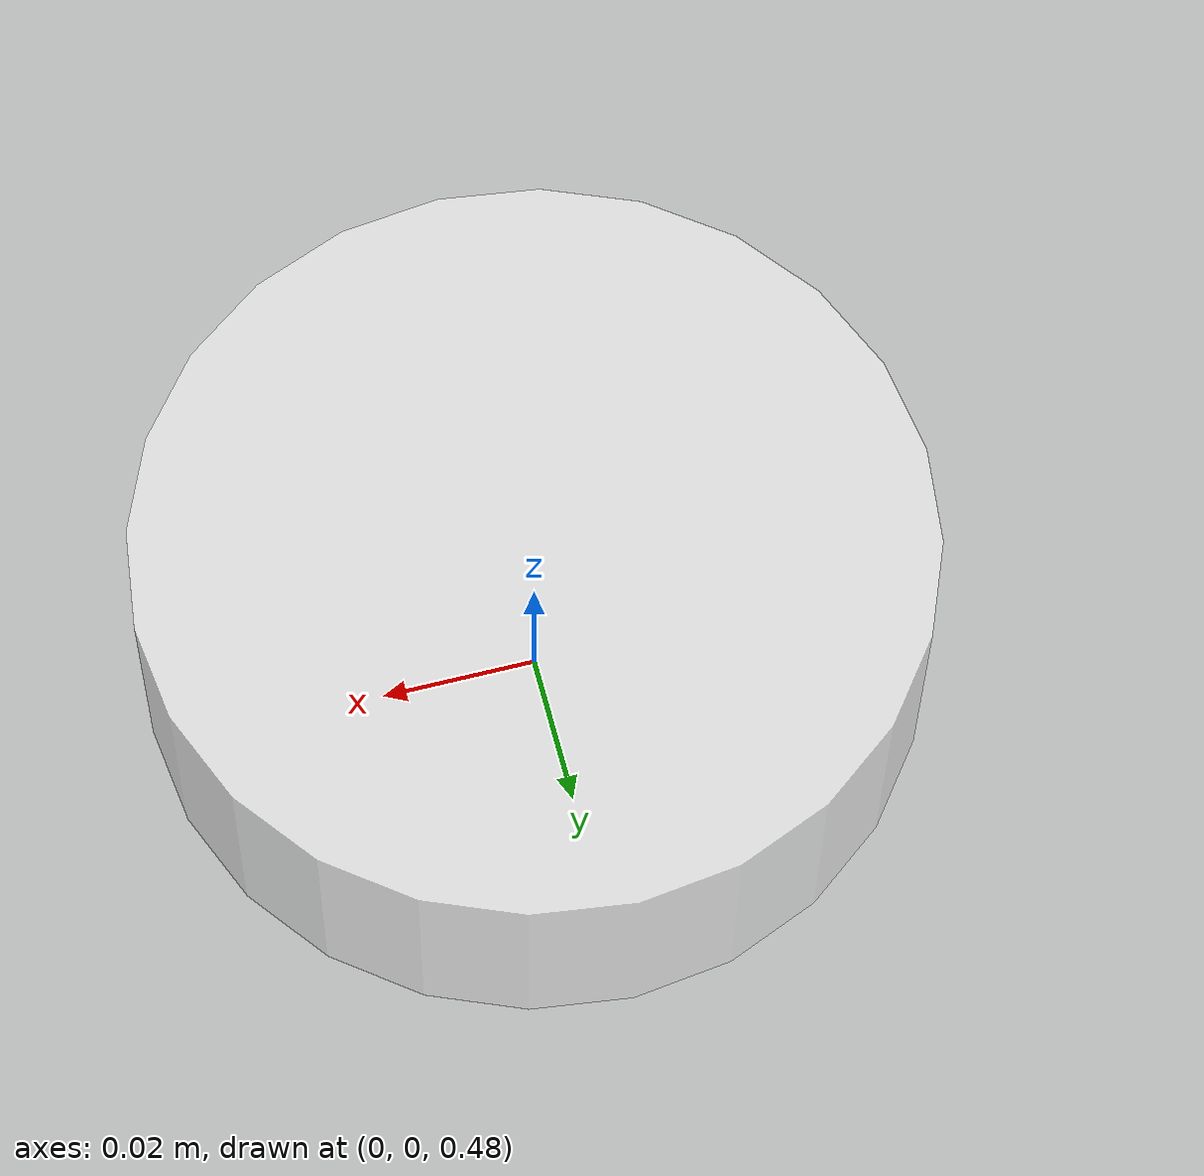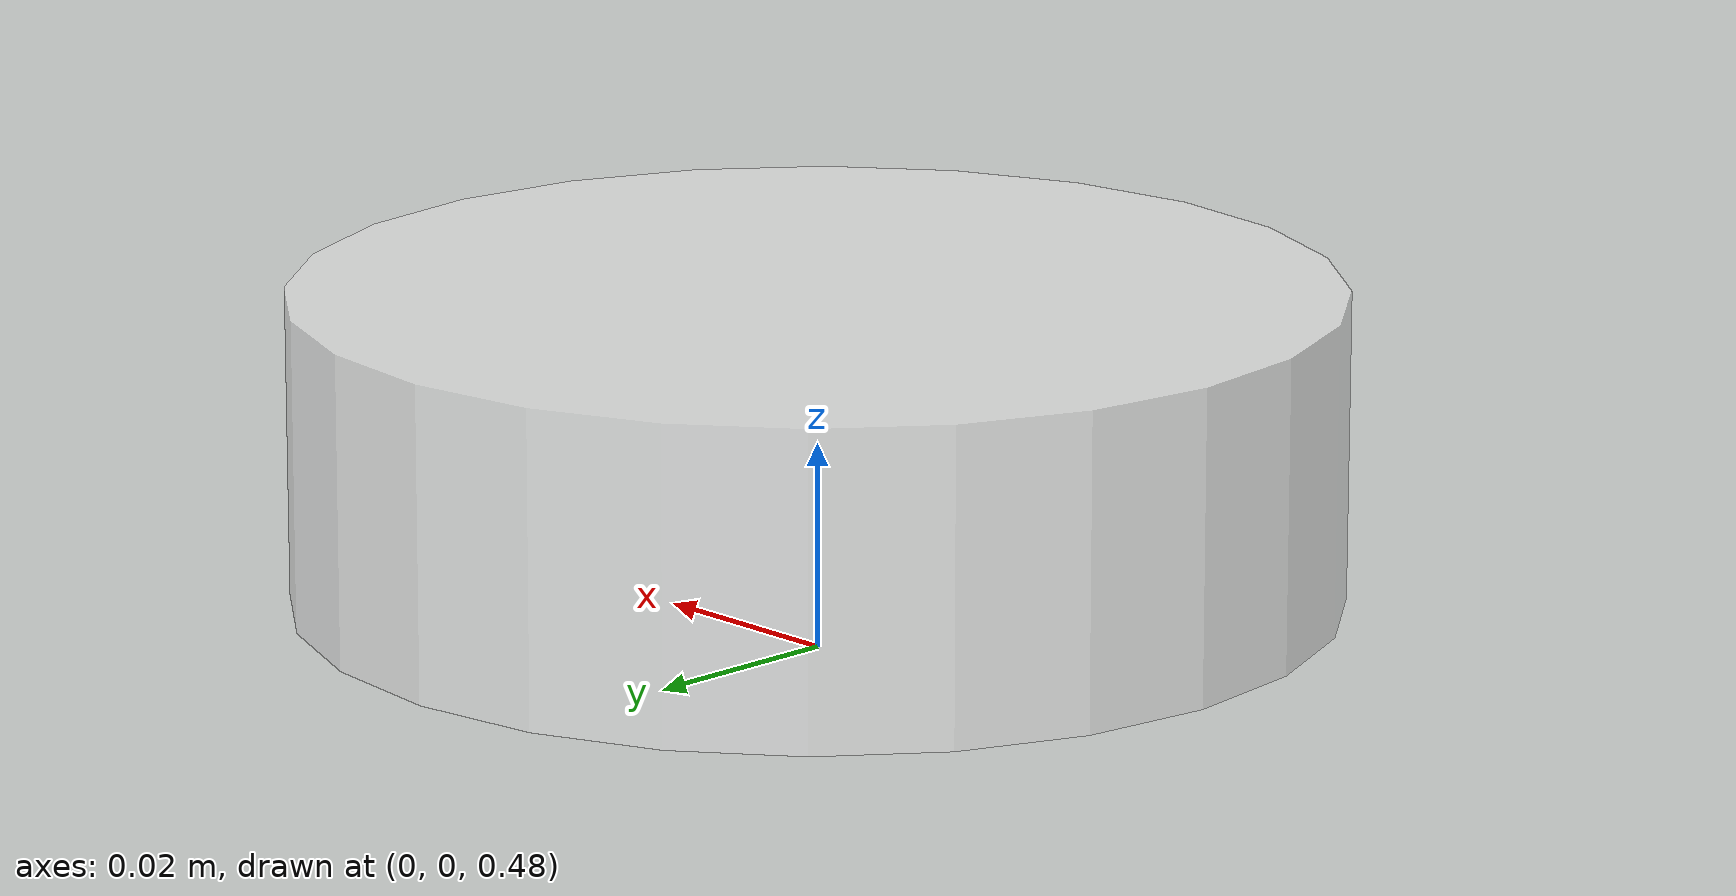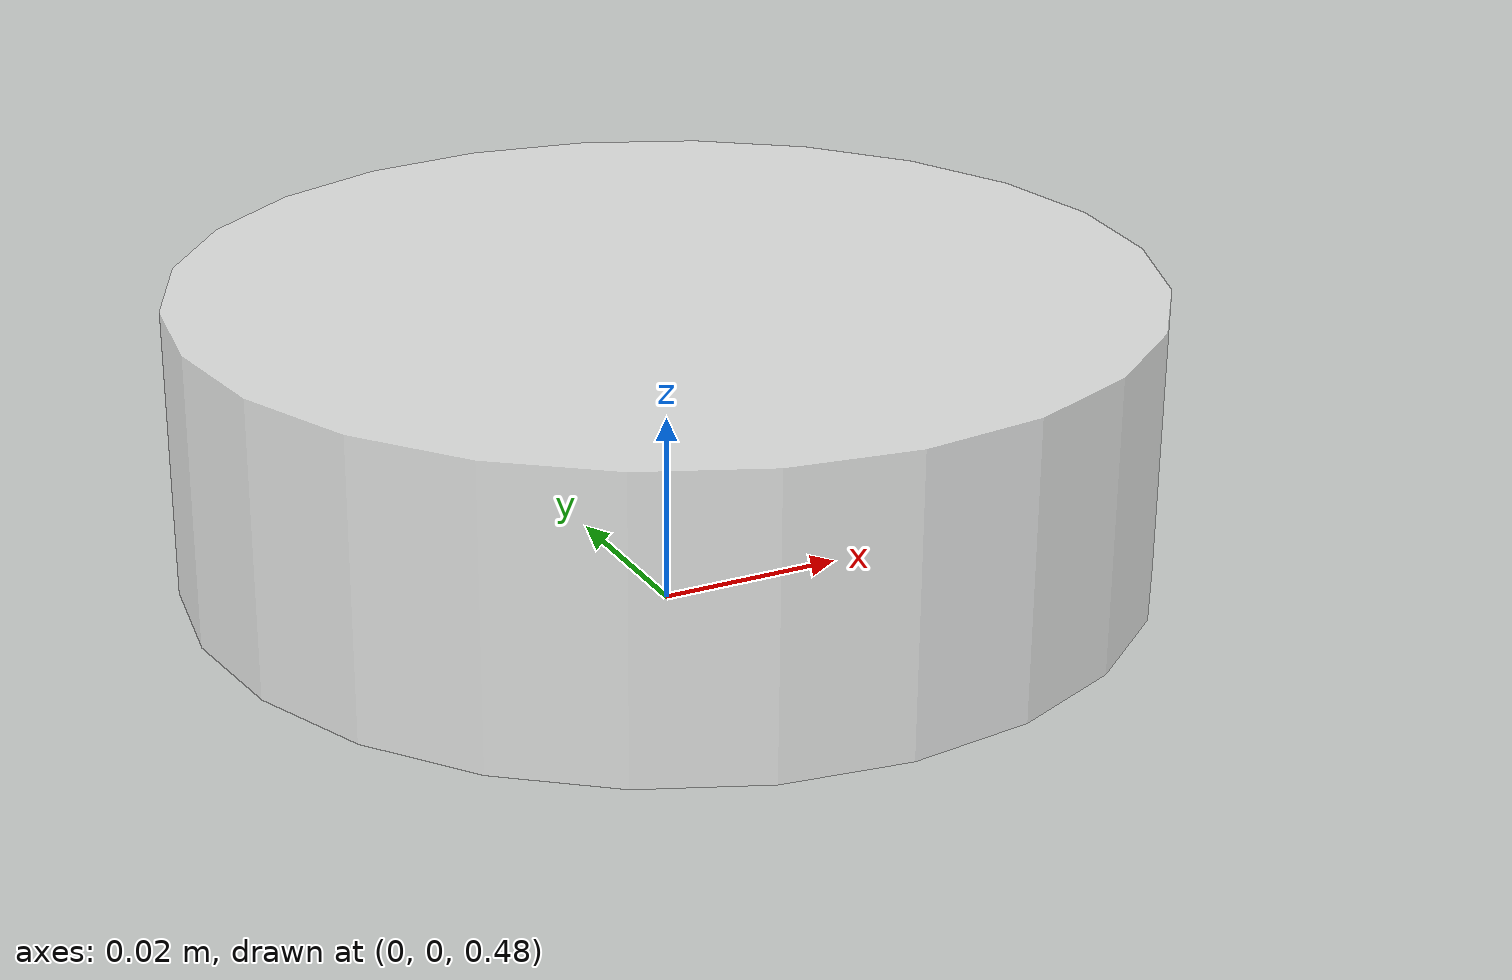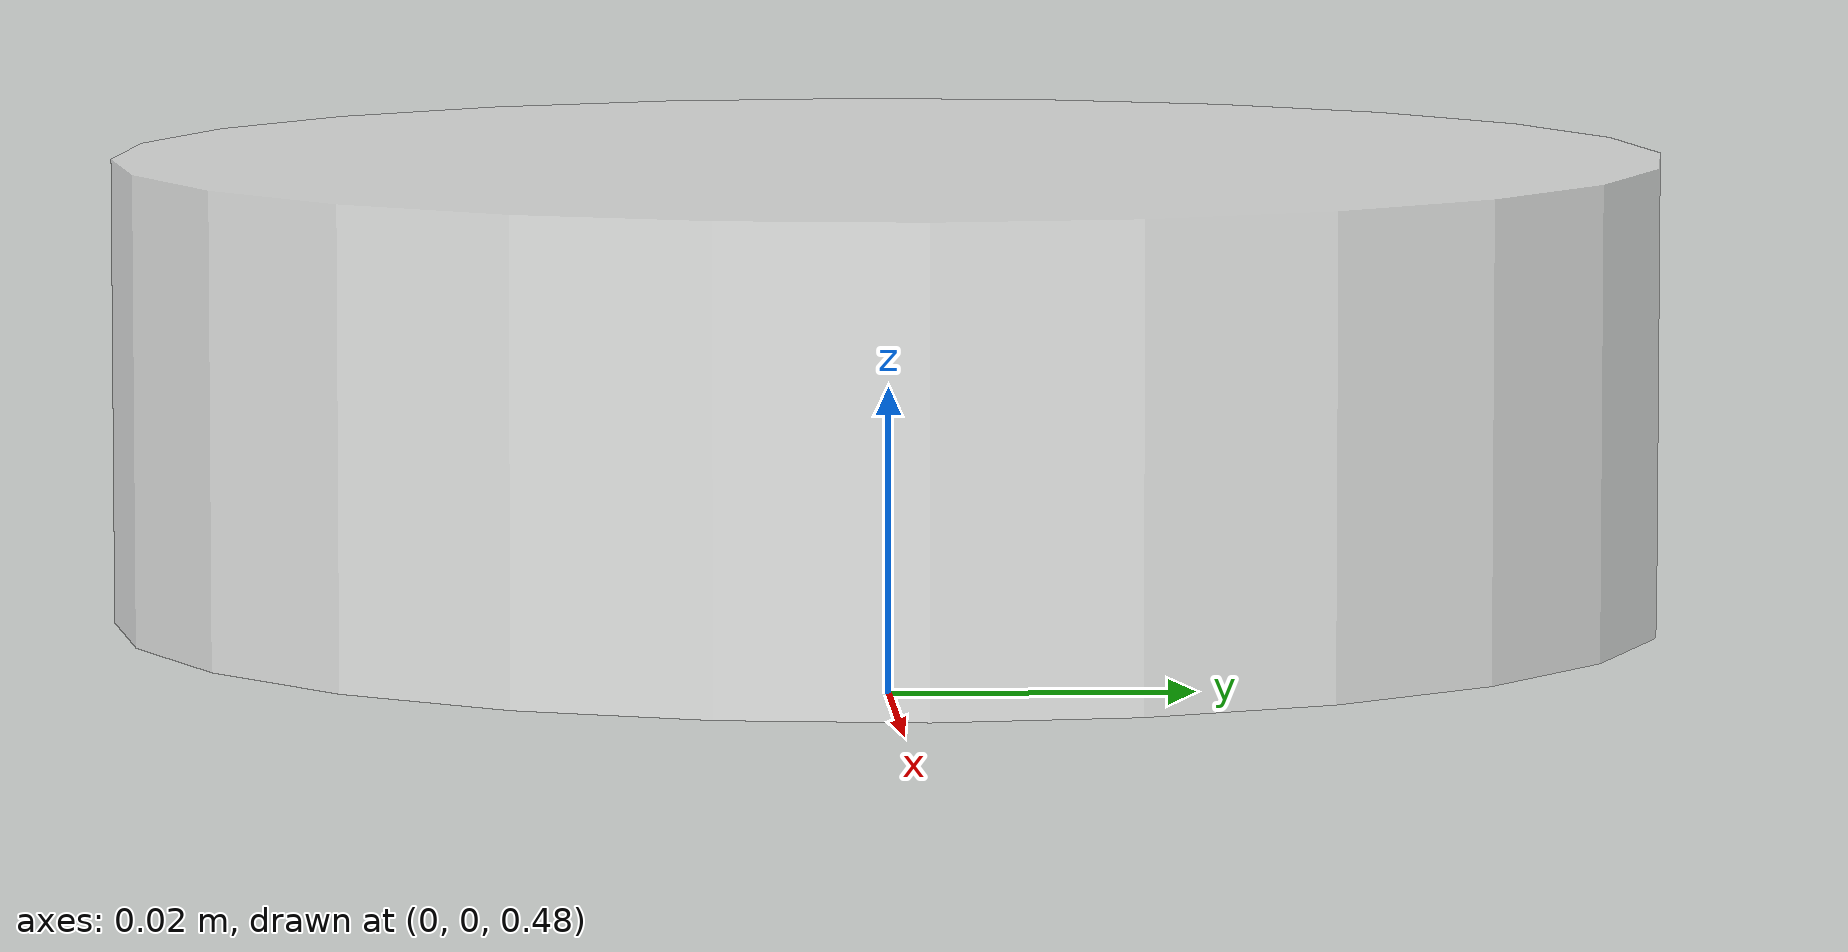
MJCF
<mujoco>
  <compiler angle="radian" autolimits="true"/>

  <default>
    <default class="stretch">
      <general biastype="affine"/>
      <default class="rangefinder_site">
        <site size="0.001 0.001" type="cylinder" rgba="1 0 0 0.7" pos="0.0 0 0" />
      </default>
    </default>
  </default>

  <worldbody>
    <body name="lidar" childclass="stretch" pos="0.0 0.0 0.5">
      <geom name="rplidar" size="0.05 0.015" type="cylinder" rgba="1 1 1 0.5" pos="0 0 0" />
      <site name="rangefinder_site_0" class="rangefinder_site" zaxis="0.000000 -1.000000 0" />
      <site name="rangefinder_site_1" class="rangefinder_site" zaxis="0.017452 -0.999848 0" />
      <site name="rangefinder_site_2" class="rangefinder_site" zaxis="0.034899 -0.999391 0" />
      <site name="rangefinder_site_3" class="rangefinder_site" zaxis="0.052336 -0.998630 0" />
      <site name="rangefinder_site_4" class="rangefinder_site" zaxis="0.069756 -0.997564 0" />
      <site name="rangefinder_site_5" class="rangefinder_site" zaxis="0.087156 -0.996195 0" />
      <site name="rangefinder_site_6" class="rangefinder_site" zaxis="0.104528 -0.994522 0" />
      <site name="rangefinder_site_7" class="rangefinder_site" zaxis="0.121869 -0.992546 0" />
      <site name="rangefinder_site_8" class="rangefinder_site" zaxis="0.139173 -0.990268 0" />
      <site name="rangefinder_site_9" class="rangefinder_site" zaxis="0.156434 -0.987688 0" />
      <site name="rangefinder_site_10" class="rangefinder_site" zaxis="0.173648 -0.984808 0" />
      <site name="rangefinder_site_11" class="rangefinder_site" zaxis="0.190809 -0.981627 0" />
      <site name="rangefinder_site_12" class="rangefinder_site" zaxis="0.207912 -0.978148 0" />
      <site name="rangefinder_site_13" class="rangefinder_site" zaxis="0.224951 -0.974370 0" />
      <site name="rangefinder_site_14" class="rangefinder_site" zaxis="0.241922 -0.970296 0" />
      <site name="rangefinder_site_15" class="rangefinder_site" zaxis="0.258819 -0.965926 0" />
      <site name="rangefinder_site_16" class="rangefinder_site" zaxis="0.275637 -0.961262 0" />
      <site name="rangefinder_site_17" class="rangefinder_site" zaxis="0.292372 -0.956305 0" />
      <site name="rangefinder_site_18" class="rangefinder_site" zaxis="0.309017 -0.951057 0" />
      <site name="rangefinder_site_19" class="rangefinder_site" zaxis="0.325568 -0.945519 0" />
      <site name="rangefinder_site_20" class="rangefinder_site" zaxis="0.342020 -0.939693 0" />
      <site name="rangefinder_site_21" class="rangefinder_site" zaxis="0.358368 -0.933580 0" />
      <site name="rangefinder_site_22" class="rangefinder_site" zaxis="0.374607 -0.927184 0" />
      <site name="rangefinder_site_23" class="rangefinder_site" zaxis="0.390731 -0.920505 0" />
      <site name="rangefinder_site_24" class="rangefinder_site" zaxis="0.406737 -0.913545 0" />
      <site name="rangefinder_site_25" class="rangefinder_site" zaxis="0.422618 -0.906308 0" />
      <site name="rangefinder_site_26" class="rangefinder_site" zaxis="0.438371 -0.898794 0" />
      <site name="rangefinder_site_27" class="rangefinder_site" zaxis="0.453990 -0.891007 0" />
      <site name="rangefinder_site_28" class="rangefinder_site" zaxis="0.469472 -0.882948 0" />
      <site name="rangefinder_site_29" class="rangefinder_site" zaxis="0.484810 -0.874620 0" />
      <site name="rangefinder_site_30" class="rangefinder_site" zaxis="0.500000 -0.866025 0" />
      <site name="rangefinder_site_31" class="rangefinder_site" zaxis="0.515038 -0.857167 0" />
      <site name="rangefinder_site_32" class="rangefinder_site" zaxis="0.529919 -0.848048 0" />
      <site name="rangefinder_site_33" class="rangefinder_site" zaxis="0.544639 -0.838671 0" />
      <site name="rangefinder_site_34" class="rangefinder_site" zaxis="0.559193 -0.829038 0" />
      <site name="rangefinder_site_35" class="rangefinder_site" zaxis="0.573576 -0.819152 0" />
      <site name="rangefinder_site_36" class="rangefinder_site" zaxis="0.587785 -0.809017 0" />
      <site name="rangefinder_site_37" class="rangefinder_site" zaxis="0.601815 -0.798636 0" />
      <site name="rangefinder_site_38" class="rangefinder_site" zaxis="0.615661 -0.788011 0" />
      <site name="rangefinder_site_39" class="rangefinder_site" zaxis="0.629320 -0.777146 0" />
      <site name="rangefinder_site_40" class="rangefinder_site" zaxis="0.642788 -0.766044 0" />
      <site name="rangefinder_site_41" class="rangefinder_site" zaxis="0.656059 -0.754710 0" />
      <site name="rangefinder_site_42" class="rangefinder_site" zaxis="0.669131 -0.743145 0" />
      <site name="rangefinder_site_43" class="rangefinder_site" zaxis="0.681998 -0.731354 0" />
      <site name="rangefinder_site_44" class="rangefinder_site" zaxis="0.694658 -0.719340 0" />
      <site name="rangefinder_site_45" class="rangefinder_site" zaxis="0.707107 -0.707107 0" />
      <site name="rangefinder_site_46" class="rangefinder_site" zaxis="0.719340 -0.694658 0" />
      <site name="rangefinder_site_47" class="rangefinder_site" zaxis="0.731354 -0.681998 0" />
      <site name="rangefinder_site_48" class="rangefinder_site" zaxis="0.743145 -0.669131 0" />
      <site name="rangefinder_site_49" class="rangefinder_site" zaxis="0.754710 -0.656059 0" />
      <site name="rangefinder_site_50" class="rangefinder_site" zaxis="0.766044 -0.642788 0" />
      <site name="rangefinder_site_51" class="rangefinder_site" zaxis="0.777146 -0.629320 0" />
      <site name="rangefinder_site_52" class="rangefinder_site" zaxis="0.788011 -0.615661 0" />
      <site name="rangefinder_site_53" class="rangefinder_site" zaxis="0.798636 -0.601815 0" />
      <site name="rangefinder_site_54" class="rangefinder_site" zaxis="0.809017 -0.587785 0" />
      <site name="rangefinder_site_55" class="rangefinder_site" zaxis="0.819152 -0.573576 0" />
      <site name="rangefinder_site_56" class="rangefinder_site" zaxis="0.829038 -0.559193 0" />
      <site name="rangefinder_site_57" class="rangefinder_site" zaxis="0.838671 -0.544639 0" />
      <site name="rangefinder_site_58" class="rangefinder_site" zaxis="0.848048 -0.529919 0" />
      <site name="rangefinder_site_59" class="rangefinder_site" zaxis="0.857167 -0.515038 0" />
      <site name="rangefinder_site_60" class="rangefinder_site" zaxis="0.866025 -0.500000 0" />
      <site name="rangefinder_site_61" class="rangefinder_site" zaxis="0.874620 -0.484810 0" />
      <site name="rangefinder_site_62" class="rangefinder_site" zaxis="0.882948 -0.469472 0" />
      <site name="rangefinder_site_63" class="rangefinder_site" zaxis="0.891007 -0.453990 0" />
      <site name="rangefinder_site_64" class="rangefinder_site" zaxis="0.898794 -0.438371 0" />
      <site name="rangefinder_site_65" class="rangefinder_site" zaxis="0.906308 -0.422618 0" />
      <site name="rangefinder_site_66" class="rangefinder_site" zaxis="0.913545 -0.406737 0" />
      <site name="rangefinder_site_67" class="rangefinder_site" zaxis="0.920505 -0.390731 0" />
      <site name="rangefinder_site_68" class="rangefinder_site" zaxis="0.927184 -0.374607 0" />
      <site name="rangefinder_site_69" class="rangefinder_site" zaxis="0.933580 -0.358368 0" />
      <site name="rangefinder_site_70" class="rangefinder_site" zaxis="0.939693 -0.342020 0" />
      <site name="rangefinder_site_71" class="rangefinder_site" zaxis="0.945519 -0.325568 0" />
      <site name="rangefinder_site_72" class="rangefinder_site" zaxis="0.951057 -0.309017 0" />
      <site name="rangefinder_site_73" class="rangefinder_site" zaxis="0.956305 -0.292372 0" />
      <site name="rangefinder_site_74" class="rangefinder_site" zaxis="0.961262 -0.275637 0" />
      <site name="rangefinder_site_75" class="rangefinder_site" zaxis="0.965926 -0.258819 0" />
      <site name="rangefinder_site_76" class="rangefinder_site" zaxis="0.970296 -0.241922 0" />
      <site name="rangefinder_site_77" class="rangefinder_site" zaxis="0.974370 -0.224951 0" />
      <site name="rangefinder_site_78" class="rangefinder_site" zaxis="0.978148 -0.207912 0" />
      <site name="rangefinder_site_79" class="rangefinder_site" zaxis="0.981627 -0.190809 0" />
      <site name="rangefinder_site_80" class="rangefinder_site" zaxis="0.984808 -0.173648 0" />
      <site name="rangefinder_site_81" class="rangefinder_site" zaxis="0.987688 -0.156434 0" />
      <site name="rangefinder_site_82" class="rangefinder_site" zaxis="0.990268 -0.139173 0" />
      <site name="rangefinder_site_83" class="rangefinder_site" zaxis="0.992546 -0.121869 0" />
      <site name="rangefinder_site_84" class="rangefinder_site" zaxis="0.994522 -0.104528 0" />
      <site name="rangefinder_site_85" class="rangefinder_site" zaxis="0.996195 -0.087156 0" />
      <site name="rangefinder_site_86" class="rangefinder_site" zaxis="0.997564 -0.069756 0" />
      <site name="rangefinder_site_87" class="rangefinder_site" zaxis="0.998630 -0.052336 0" />
      <site name="rangefinder_site_88" class="rangefinder_site" zaxis="0.999391 -0.034899 0" />
      <site name="rangefinder_site_89" class="rangefinder_site" zaxis="0.999848 -0.017452 0" />
      <site name="rangefinder_site_90" class="rangefinder_site" zaxis="1.000000 0.000000 0" />
      <site name="rangefinder_site_91" class="rangefinder_site" zaxis="0.999848 0.017452 0" />
      <site name="rangefinder_site_92" class="rangefinder_site" zaxis="0.999391 0.034899 0" />
      <site name="rangefinder_site_93" class="rangefinder_site" zaxis="0.998630 0.052336 0" />
      <site name="rangefinder_site_94" class="rangefinder_site" zaxis="0.997564 0.069756 0" />
      <site name="rangefinder_site_95" class="rangefinder_site" zaxis="0.996195 0.087156 0" />
      <site name="rangefinder_site_96" class="rangefinder_site" zaxis="0.994522 0.104528 0" />
      <site name="rangefinder_site_97" class="rangefinder_site" zaxis="0.992546 0.121869 0" />
      <site name="rangefinder_site_98" class="rangefinder_site" zaxis="0.990268 0.139173 0" />
      <site name="rangefinder_site_99" class="rangefinder_site" zaxis="0.987688 0.156434 0" />
      <site name="rangefinder_site_100" class="rangefinder_site" zaxis="0.984808 0.173648 0" />
      <site name="rangefinder_site_101" class="rangefinder_site" zaxis="0.981627 0.190809 0" />
      <site name="rangefinder_site_102" class="rangefinder_site" zaxis="0.978148 0.207912 0" />
      <site name="rangefinder_site_103" class="rangefinder_site" zaxis="0.974370 0.224951 0" />
      <site name="rangefinder_site_104" class="rangefinder_site" zaxis="0.970296 0.241922 0" />
      <site name="rangefinder_site_105" class="rangefinder_site" zaxis="0.965926 0.258819 0" />
      <site name="rangefinder_site_106" class="rangefinder_site" zaxis="0.961262 0.275637 0" />
      <site name="rangefinder_site_107" class="rangefinder_site" zaxis="0.956305 0.292372 0" />
      <site name="rangefinder_site_108" class="rangefinder_site" zaxis="0.951057 0.309017 0" />
      <site name="rangefinder_site_109" class="rangefinder_site" zaxis="0.945519 0.325568 0" />
      <site name="rangefinder_site_110" class="rangefinder_site" zaxis="0.939693 0.342020 0" />
      <site name="rangefinder_site_111" class="rangefinder_site" zaxis="0.933580 0.358368 0" />
      <site name="rangefinder_site_112" class="rangefinder_site" zaxis="0.927184 0.374607 0" />
      <site name="rangefinder_site_113" class="rangefinder_site" zaxis="0.920505 0.390731 0" />
      <site name="rangefinder_site_114" class="rangefinder_site" zaxis="0.913545 0.406737 0" />
      <site name="rangefinder_site_115" class="rangefinder_site" zaxis="0.906308 0.422618 0" />
      <site name="rangefinder_site_116" class="rangefinder_site" zaxis="0.898794 0.438371 0" />
      <site name="rangefinder_site_117" class="rangefinder_site" zaxis="0.891007 0.453990 0" />
      <site name="rangefinder_site_118" class="rangefinder_site" zaxis="0.882948 0.469472 0" />
      <site name="rangefinder_site_119" class="rangefinder_site" zaxis="0.874620 0.484810 0" />
      <site name="rangefinder_site_120" class="rangefinder_site" zaxis="0.866025 0.500000 0" />
      <site name="rangefinder_site_121" class="rangefinder_site" zaxis="0.857167 0.515038 0" />
      <site name="rangefinder_site_122" class="rangefinder_site" zaxis="0.848048 0.529919 0" />
      <site name="rangefinder_site_123" class="rangefinder_site" zaxis="0.838671 0.544639 0" />
      <site name="rangefinder_site_124" class="rangefinder_site" zaxis="0.829038 0.559193 0" />
      <site name="rangefinder_site_125" class="rangefinder_site" zaxis="0.819152 0.573576 0" />
      <site name="rangefinder_site_126" class="rangefinder_site" zaxis="0.809017 0.587785 0" />
      <site name="rangefinder_site_127" class="rangefinder_site" zaxis="0.798636 0.601815 0" />
      <site name="rangefinder_site_128" class="rangefinder_site" zaxis="0.788011 0.615661 0" />
      <site name="rangefinder_site_129" class="rangefinder_site" zaxis="0.777146 0.629320 0" />
      <site name="rangefinder_site_130" class="rangefinder_site" zaxis="0.766044 0.642788 0" />
      <site name="rangefinder_site_131" class="rangefinder_site" zaxis="0.754710 0.656059 0" />
      <site name="rangefinder_site_132" class="rangefinder_site" zaxis="0.743145 0.669131 0" />
      <site name="rangefinder_site_133" class="rangefinder_site" zaxis="0.731354 0.681998 0" />
      <site name="rangefinder_site_134" class="rangefinder_site" zaxis="0.719340 0.694658 0" />
      <site name="rangefinder_site_135" class="rangefinder_site" zaxis="0.707107 0.707107 0" />
      <site name="rangefinder_site_136" class="rangefinder_site" zaxis="0.694658 0.719340 0" />
      <site name="rangefinder_site_137" class="rangefinder_site" zaxis="0.681998 0.731354 0" />
      <site name="rangefinder_site_138" class="rangefinder_site" zaxis="0.669131 0.743145 0" />
      <site name="rangefinder_site_139" class="rangefinder_site" zaxis="0.656059 0.754710 0" />
      <site name="rangefinder_site_140" class="rangefinder_site" zaxis="0.642788 0.766044 0" />
      <site name="rangefinder_site_141" class="rangefinder_site" zaxis="0.629320 0.777146 0" />
      <site name="rangefinder_site_142" class="rangefinder_site" zaxis="0.615661 0.788011 0" />
      <site name="rangefinder_site_143" class="rangefinder_site" zaxis="0.601815 0.798636 0" />
      <site name="rangefinder_site_144" class="rangefinder_site" zaxis="0.587785 0.809017 0" />
      <site name="rangefinder_site_145" class="rangefinder_site" zaxis="0.573576 0.819152 0" />
      <site name="rangefinder_site_146" class="rangefinder_site" zaxis="0.559193 0.829038 0" />
      <site name="rangefinder_site_147" class="rangefinder_site" zaxis="0.544639 0.838671 0" />
      <site name="rangefinder_site_148" class="rangefinder_site" zaxis="0.529919 0.848048 0" />
      <site name="rangefinder_site_149" class="rangefinder_site" zaxis="0.515038 0.857167 0" />
      <site name="rangefinder_site_150" class="rangefinder_site" zaxis="0.500000 0.866025 0" />
      <site name="rangefinder_site_151" class="rangefinder_site" zaxis="0.484810 0.874620 0" />
      <site name="rangefinder_site_152" class="rangefinder_site" zaxis="0.469472 0.882948 0" />
      <site name="rangefinder_site_153" class="rangefinder_site" zaxis="0.453990 0.891007 0" />
      <site name="rangefinder_site_154" class="rangefinder_site" zaxis="0.438371 0.898794 0" />
      <site name="rangefinder_site_155" class="rangefinder_site" zaxis="0.422618 0.906308 0" />
      <site name="rangefinder_site_156" class="rangefinder_site" zaxis="0.406737 0.913545 0" />
      <site name="rangefinder_site_157" class="rangefinder_site" zaxis="0.390731 0.920505 0" />
      <site name="rangefinder_site_158" class="rangefinder_site" zaxis="0.374607 0.927184 0" />
      <site name="rangefinder_site_159" class="rangefinder_site" zaxis="0.358368 0.933580 0" />
      <site name="rangefinder_site_160" class="rangefinder_site" zaxis="0.342020 0.939693 0" />
      <site name="rangefinder_site_161" class="rangefinder_site" zaxis="0.325568 0.945519 0" />
      <site name="rangefinder_site_162" class="rangefinder_site" zaxis="0.309017 0.951057 0" />
      <site name="rangefinder_site_163" class="rangefinder_site" zaxis="0.292372 0.956305 0" />
      <site name="rangefinder_site_164" class="rangefinder_site" zaxis="0.275637 0.961262 0" />
      <site name="rangefinder_site_165" class="rangefinder_site" zaxis="0.258819 0.965926 0" />
      <site name="rangefinder_site_166" class="rangefinder_site" zaxis="0.241922 0.970296 0" />
      <site name="rangefinder_site_167" class="rangefinder_site" zaxis="0.224951 0.974370 0" />
      <site name="rangefinder_site_168" class="rangefinder_site" zaxis="0.207912 0.978148 0" />
      <site name="rangefinder_site_169" class="rangefinder_site" zaxis="0.190809 0.981627 0" />
      <site name="rangefinder_site_170" class="rangefinder_site" zaxis="0.173648 0.984808 0" />
      <site name="rangefinder_site_171" class="rangefinder_site" zaxis="0.156434 0.987688 0" />
      <site name="rangefinder_site_172" class="rangefinder_site" zaxis="0.139173 0.990268 0" />
      <site name="rangefinder_site_173" class="rangefinder_site" zaxis="0.121869 0.992546 0" />
      <site name="rangefinder_site_174" class="rangefinder_site" zaxis="0.104528 0.994522 0" />
      <site name="rangefinder_site_175" class="rangefinder_site" zaxis="0.087156 0.996195 0" />
      <site name="rangefinder_site_176" class="rangefinder_site" zaxis="0.069756 0.997564 0" />
      <site name="rangefinder_site_177" class="rangefinder_site" zaxis="0.052336 0.998630 0" />
      <site name="rangefinder_site_178" class="rangefinder_site" zaxis="0.034899 0.999391 0" />
      <site name="rangefinder_site_179" class="rangefinder_site" zaxis="0.017452 0.999848 0" />
      <site name="rangefinder_site_180" class="rangefinder_site" zaxis="0.000000 1.000000 0" />
      <site name="rangefinder_site_181" class="rangefinder_site" zaxis="-0.017452 0.999848 0" />
      <site name="rangefinder_site_182" class="rangefinder_site" zaxis="-0.034899 0.999391 0" />
      <site name="rangefinder_site_183" class="rangefinder_site" zaxis="-0.052336 0.998630 0" />
      <site name="rangefinder_site_184" class="rangefinder_site" zaxis="-0.069756 0.997564 0" />
      <site name="rangefinder_site_185" class="rangefinder_site" zaxis="-0.087156 0.996195 0" />
      <site name="rangefinder_site_186" class="rangefinder_site" zaxis="-0.104528 0.994522 0" />
      <site name="rangefinder_site_187" class="rangefinder_site" zaxis="-0.121869 0.992546 0" />
      <site name="rangefinder_site_188" class="rangefinder_site" zaxis="-0.139173 0.990268 0" />
      <site name="rangefinder_site_189" class="rangefinder_site" zaxis="-0.156434 0.987688 0" />
      <site name="rangefinder_site_190" class="rangefinder_site" zaxis="-0.173648 0.984808 0" />
      <site name="rangefinder_site_191" class="rangefinder_site" zaxis="-0.190809 0.981627 0" />
      <site name="rangefinder_site_192" class="rangefinder_site" zaxis="-0.207912 0.978148 0" />
      <site name="rangefinder_site_193" class="rangefinder_site" zaxis="-0.224951 0.974370 0" />
      <site name="rangefinder_site_194" class="rangefinder_site" zaxis="-0.241922 0.970296 0" />
      <site name="rangefinder_site_195" class="rangefinder_site" zaxis="-0.258819 0.965926 0" />
      <site name="rangefinder_site_196" class="rangefinder_site" zaxis="-0.275637 0.961262 0" />
      <site name="rangefinder_site_197" class="rangefinder_site" zaxis="-0.292372 0.956305 0" />
      <site name="rangefinder_site_198" class="rangefinder_site" zaxis="-0.309017 0.951057 0" />
      <site name="rangefinder_site_199" class="rangefinder_site" zaxis="-0.325568 0.945519 0" />
      <site name="rangefinder_site_200" class="rangefinder_site" zaxis="-0.342020 0.939693 0" />
      <site name="rangefinder_site_201" class="rangefinder_site" zaxis="-0.358368 0.933580 0" />
      <site name="rangefinder_site_202" class="rangefinder_site" zaxis="-0.374607 0.927184 0" />
      <site name="rangefinder_site_203" class="rangefinder_site" zaxis="-0.390731 0.920505 0" />
      <site name="rangefinder_site_204" class="rangefinder_site" zaxis="-0.406737 0.913545 0" />
      <site name="rangefinder_site_205" class="rangefinder_site" zaxis="-0.422618 0.906308 0" />
      <site name="rangefinder_site_206" class="rangefinder_site" zaxis="-0.438371 0.898794 0" />
      <site name="rangefinder_site_207" class="rangefinder_site" zaxis="-0.453990 0.891007 0" />
      <site name="rangefinder_site_208" class="rangefinder_site" zaxis="-0.469472 0.882948 0" />
      <site name="rangefinder_site_209" class="rangefinder_site" zaxis="-0.484810 0.874620 0" />
      <site name="rangefinder_site_210" class="rangefinder_site" zaxis="-0.500000 0.866025 0" />
      <site name="rangefinder_site_211" class="rangefinder_site" zaxis="-0.515038 0.857167 0" />
      <site name="rangefinder_site_212" class="rangefinder_site" zaxis="-0.529919 0.848048 0" />
      <site name="rangefinder_site_213" class="rangefinder_site" zaxis="-0.544639 0.838671 0" />
      <site name="rangefinder_site_214" class="rangefinder_site" zaxis="-0.559193 0.829038 0" />
      <site name="rangefinder_site_215" class="rangefinder_site" zaxis="-0.573576 0.819152 0" />
      <site name="rangefinder_site_216" class="rangefinder_site" zaxis="-0.587785 0.809017 0" />
      <site name="rangefinder_site_217" class="rangefinder_site" zaxis="-0.601815 0.798636 0" />
      <site name="rangefinder_site_218" class="rangefinder_site" zaxis="-0.615661 0.788011 0" />
      <site name="rangefinder_site_219" class="rangefinder_site" zaxis="-0.629320 0.777146 0" />
      <site name="rangefinder_site_220" class="rangefinder_site" zaxis="-0.642788 0.766044 0" />
      <site name="rangefinder_site_221" class="rangefinder_site" zaxis="-0.656059 0.754710 0" />
      <site name="rangefinder_site_222" class="rangefinder_site" zaxis="-0.669131 0.743145 0" />
      <site name="rangefinder_site_223" class="rangefinder_site" zaxis="-0.681998 0.731354 0" />
      <site name="rangefinder_site_224" class="rangefinder_site" zaxis="-0.694658 0.719340 0" />
      <site name="rangefinder_site_225" class="rangefinder_site" zaxis="-0.707107 0.707107 0" />
      <site name="rangefinder_site_226" class="rangefinder_site" zaxis="-0.719340 0.694658 0" />
      <site name="rangefinder_site_227" class="rangefinder_site" zaxis="-0.731354 0.681998 0" />
      <site name="rangefinder_site_228" class="rangefinder_site" zaxis="-0.743145 0.669131 0" />
      <site name="rangefinder_site_229" class="rangefinder_site" zaxis="-0.754710 0.656059 0" />
      <site name="rangefinder_site_230" class="rangefinder_site" zaxis="-0.766044 0.642788 0" />
      <site name="rangefinder_site_231" class="rangefinder_site" zaxis="-0.777146 0.629320 0" />
      <site name="rangefinder_site_232" class="rangefinder_site" zaxis="-0.788011 0.615661 0" />
      <site name="rangefinder_site_233" class="rangefinder_site" zaxis="-0.798636 0.601815 0" />
      <site name="rangefinder_site_234" class="rangefinder_site" zaxis="-0.809017 0.587785 0" />
      <site name="rangefinder_site_235" class="rangefinder_site" zaxis="-0.819152 0.573576 0" />
      <site name="rangefinder_site_236" class="rangefinder_site" zaxis="-0.829038 0.559193 0" />
      <site name="rangefinder_site_237" class="rangefinder_site" zaxis="-0.838671 0.544639 0" />
      <site name="rangefinder_site_238" class="rangefinder_site" zaxis="-0.848048 0.529919 0" />
      <site name="rangefinder_site_239" class="rangefinder_site" zaxis="-0.857167 0.515038 0" />
      <site name="rangefinder_site_240" class="rangefinder_site" zaxis="-0.866025 0.500000 0" />
      <site name="rangefinder_site_241" class="rangefinder_site" zaxis="-0.874620 0.484810 0" />
      <site name="rangefinder_site_242" class="rangefinder_site" zaxis="-0.882948 0.469472 0" />
      <site name="rangefinder_site_243" class="rangefinder_site" zaxis="-0.891007 0.453990 0" />
      <site name="rangefinder_site_244" class="rangefinder_site" zaxis="-0.898794 0.438371 0" />
      <site name="rangefinder_site_245" class="rangefinder_site" zaxis="-0.906308 0.422618 0" />
      <site name="rangefinder_site_246" class="rangefinder_site" zaxis="-0.913545 0.406737 0" />
      <site name="rangefinder_site_247" class="rangefinder_site" zaxis="-0.920505 0.390731 0" />
      <site name="rangefinder_site_248" class="rangefinder_site" zaxis="-0.927184 0.374607 0" />
      <site name="rangefinder_site_249" class="rangefinder_site" zaxis="-0.933580 0.358368 0" />
      <site name="rangefinder_site_250" class="rangefinder_site" zaxis="-0.939693 0.342020 0" />
      <site name="rangefinder_site_251" class="rangefinder_site" zaxis="-0.945519 0.325568 0" />
      <site name="rangefinder_site_252" class="rangefinder_site" zaxis="-0.951057 0.309017 0" />
      <site name="rangefinder_site_253" class="rangefinder_site" zaxis="-0.956305 0.292372 0" />
      <site name="rangefinder_site_254" class="rangefinder_site" zaxis="-0.961262 0.275637 0" />
      <site name="rangefinder_site_255" class="rangefinder_site" zaxis="-0.965926 0.258819 0" />
      <site name="rangefinder_site_256" class="rangefinder_site" zaxis="-0.970296 0.241922 0" />
      <site name="rangefinder_site_257" class="rangefinder_site" zaxis="-0.974370 0.224951 0" />
      <site name="rangefinder_site_258" class="rangefinder_site" zaxis="-0.978148 0.207912 0" />
      <site name="rangefinder_site_259" class="rangefinder_site" zaxis="-0.981627 0.190809 0" />
      <site name="rangefinder_site_260" class="rangefinder_site" zaxis="-0.984808 0.173648 0" />
      <site name="rangefinder_site_261" class="rangefinder_site" zaxis="-0.987688 0.156434 0" />
      <site name="rangefinder_site_262" class="rangefinder_site" zaxis="-0.990268 0.139173 0" />
      <site name="rangefinder_site_263" class="rangefinder_site" zaxis="-0.992546 0.121869 0" />
      <site name="rangefinder_site_264" class="rangefinder_site" zaxis="-0.994522 0.104528 0" />
      <site name="rangefinder_site_265" class="rangefinder_site" zaxis="-0.996195 0.087156 0" />
      <site name="rangefinder_site_266" class="rangefinder_site" zaxis="-0.997564 0.069756 0" />
      <site name="rangefinder_site_267" class="rangefinder_site" zaxis="-0.998630 0.052336 0" />
      <site name="rangefinder_site_268" class="rangefinder_site" zaxis="-0.999391 0.034899 0" />
      <site name="rangefinder_site_269" class="rangefinder_site" zaxis="-0.999848 0.017452 0" />
      <site name="rangefinder_site_270" class="rangefinder_site" zaxis="-1.000000 0.000000 0" />
      <site name="rangefinder_site_271" class="rangefinder_site" zaxis="-0.999848 -0.017452 0" />
      <site name="rangefinder_site_272" class="rangefinder_site" zaxis="-0.999391 -0.034899 0" />
      <site name="rangefinder_site_273" class="rangefinder_site" zaxis="-0.998630 -0.052336 0" />
      <site name="rangefinder_site_274" class="rangefinder_site" zaxis="-0.997564 -0.069756 0" />
      <site name="rangefinder_site_275" class="rangefinder_site" zaxis="-0.996195 -0.087156 0" />
      <site name="rangefinder_site_276" class="rangefinder_site" zaxis="-0.994522 -0.104528 0" />
      <site name="rangefinder_site_277" class="rangefinder_site" zaxis="-0.992546 -0.121869 0" />
      <site name="rangefinder_site_278" class="rangefinder_site" zaxis="-0.990268 -0.139173 0" />
      <site name="rangefinder_site_279" class="rangefinder_site" zaxis="-0.987688 -0.156434 0" />
      <site name="rangefinder_site_280" class="rangefinder_site" zaxis="-0.984808 -0.173648 0" />
      <site name="rangefinder_site_281" class="rangefinder_site" zaxis="-0.981627 -0.190809 0" />
      <site name="rangefinder_site_282" class="rangefinder_site" zaxis="-0.978148 -0.207912 0" />
      <site name="rangefinder_site_283" class="rangefinder_site" zaxis="-0.974370 -0.224951 0" />
      <site name="rangefinder_site_284" class="rangefinder_site" zaxis="-0.970296 -0.241922 0" />
      <site name="rangefinder_site_285" class="rangefinder_site" zaxis="-0.965926 -0.258819 0" />
      <site name="rangefinder_site_286" class="rangefinder_site" zaxis="-0.961262 -0.275637 0" />
      <site name="rangefinder_site_287" class="rangefinder_site" zaxis="-0.956305 -0.292372 0" />
      <site name="rangefinder_site_288" class="rangefinder_site" zaxis="-0.951057 -0.309017 0" />
      <site name="rangefinder_site_289" class="rangefinder_site" zaxis="-0.945519 -0.325568 0" />
      <site name="rangefinder_site_290" class="rangefinder_site" zaxis="-0.939693 -0.342020 0" />
      <site name="rangefinder_site_291" class="rangefinder_site" zaxis="-0.933580 -0.358368 0" />
      <site name="rangefinder_site_292" class="rangefinder_site" zaxis="-0.927184 -0.374607 0" />
      <site name="rangefinder_site_293" class="rangefinder_site" zaxis="-0.920505 -0.390731 0" />
      <site name="rangefinder_site_294" class="rangefinder_site" zaxis="-0.913545 -0.406737 0" />
      <site name="rangefinder_site_295" class="rangefinder_site" zaxis="-0.906308 -0.422618 0" />
      <site name="rangefinder_site_296" class="rangefinder_site" zaxis="-0.898794 -0.438371 0" />
      <site name="rangefinder_site_297" class="rangefinder_site" zaxis="-0.891007 -0.453990 0" />
      <site name="rangefinder_site_298" class="rangefinder_site" zaxis="-0.882948 -0.469472 0" />
      <site name="rangefinder_site_299" class="rangefinder_site" zaxis="-0.874620 -0.484810 0" />
      <site name="rangefinder_site_300" class="rangefinder_site" zaxis="-0.866025 -0.500000 0" />
      <site name="rangefinder_site_301" class="rangefinder_site" zaxis="-0.857167 -0.515038 0" />
      <site name="rangefinder_site_302" class="rangefinder_site" zaxis="-0.848048 -0.529919 0" />
      <site name="rangefinder_site_303" class="rangefinder_site" zaxis="-0.838671 -0.544639 0" />
      <site name="rangefinder_site_304" class="rangefinder_site" zaxis="-0.829038 -0.559193 0" />
      <site name="rangefinder_site_305" class="rangefinder_site" zaxis="-0.819152 -0.573576 0" />
      <site name="rangefinder_site_306" class="rangefinder_site" zaxis="-0.809017 -0.587785 0" />
      <site name="rangefinder_site_307" class="rangefinder_site" zaxis="-0.798636 -0.601815 0" />
      <site name="rangefinder_site_308" class="rangefinder_site" zaxis="-0.788011 -0.615661 0" />
      <site name="rangefinder_site_309" class="rangefinder_site" zaxis="-0.777146 -0.629320 0" />
      <site name="rangefinder_site_310" class="rangefinder_site" zaxis="-0.766044 -0.642788 0" />
      <site name="rangefinder_site_311" class="rangefinder_site" zaxis="-0.754710 -0.656059 0" />
      <site name="rangefinder_site_312" class="rangefinder_site" zaxis="-0.743145 -0.669131 0" />
      <site name="rangefinder_site_313" class="rangefinder_site" zaxis="-0.731354 -0.681998 0" />
      <site name="rangefinder_site_314" class="rangefinder_site" zaxis="-0.719340 -0.694658 0" />
      <site name="rangefinder_site_315" class="rangefinder_site" zaxis="-0.707107 -0.707107 0" />
      <site name="rangefinder_site_316" class="rangefinder_site" zaxis="-0.694658 -0.719340 0" />
      <site name="rangefinder_site_317" class="rangefinder_site" zaxis="-0.681998 -0.731354 0" />
      <site name="rangefinder_site_318" class="rangefinder_site" zaxis="-0.669131 -0.743145 0" />
      <site name="rangefinder_site_319" class="rangefinder_site" zaxis="-0.656059 -0.754710 0" />
      <site name="rangefinder_site_320" class="rangefinder_site" zaxis="-0.642788 -0.766044 0" />
      <site name="rangefinder_site_321" class="rangefinder_site" zaxis="-0.629320 -0.777146 0" />
      <site name="rangefinder_site_322" class="rangefinder_site" zaxis="-0.615661 -0.788011 0" />
      <site name="rangefinder_site_323" class="rangefinder_site" zaxis="-0.601815 -0.798636 0" />
      <site name="rangefinder_site_324" class="rangefinder_site" zaxis="-0.587785 -0.809017 0" />
      <site name="rangefinder_site_325" class="rangefinder_site" zaxis="-0.573576 -0.819152 0" />
      <site name="rangefinder_site_326" class="rangefinder_site" zaxis="-0.559193 -0.829038 0" />
      <site name="rangefinder_site_327" class="rangefinder_site" zaxis="-0.544639 -0.838671 0" />
      <site name="rangefinder_site_328" class="rangefinder_site" zaxis="-0.529919 -0.848048 0" />
      <site name="rangefinder_site_329" class="rangefinder_site" zaxis="-0.515038 -0.857167 0" />
      <site name="rangefinder_site_330" class="rangefinder_site" zaxis="-0.500000 -0.866025 0" />
      <site name="rangefinder_site_331" class="rangefinder_site" zaxis="-0.484810 -0.874620 0" />
      <site name="rangefinder_site_332" class="rangefinder_site" zaxis="-0.469472 -0.882948 0" />
      <site name="rangefinder_site_333" class="rangefinder_site" zaxis="-0.453990 -0.891007 0" />
      <site name="rangefinder_site_334" class="rangefinder_site" zaxis="-0.438371 -0.898794 0" />
      <site name="rangefinder_site_335" class="rangefinder_site" zaxis="-0.422618 -0.906308 0" />
      <site name="rangefinder_site_336" class="rangefinder_site" zaxis="-0.406737 -0.913545 0" />
      <site name="rangefinder_site_337" class="rangefinder_site" zaxis="-0.390731 -0.920505 0" />
      <site name="rangefinder_site_338" class="rangefinder_site" zaxis="-0.374607 -0.927184 0" />
      <site name="rangefinder_site_339" class="rangefinder_site" zaxis="-0.358368 -0.933580 0" />
      <site name="rangefinder_site_340" class="rangefinder_site" zaxis="-0.342020 -0.939693 0" />
      <site name="rangefinder_site_341" class="rangefinder_site" zaxis="-0.325568 -0.945519 0" />
      <site name="rangefinder_site_342" class="rangefinder_site" zaxis="-0.309017 -0.951057 0" />
      <site name="rangefinder_site_343" class="rangefinder_site" zaxis="-0.292372 -0.956305 0" />
      <site name="rangefinder_site_344" class="rangefinder_site" zaxis="-0.275637 -0.961262 0" />
      <site name="rangefinder_site_345" class="rangefinder_site" zaxis="-0.258819 -0.965926 0" />
      <site name="rangefinder_site_346" class="rangefinder_site" zaxis="-0.241922 -0.970296 0" />
      <site name="rangefinder_site_347" class="rangefinder_site" zaxis="-0.224951 -0.974370 0" />
      <site name="rangefinder_site_348" class="rangefinder_site" zaxis="-0.207912 -0.978148 0" />
      <site name="rangefinder_site_349" class="rangefinder_site" zaxis="-0.190809 -0.981627 0" />
      <site name="rangefinder_site_350" class="rangefinder_site" zaxis="-0.173648 -0.984808 0" />
      <site name="rangefinder_site_351" class="rangefinder_site" zaxis="-0.156434 -0.987688 0" />
      <site name="rangefinder_site_352" class="rangefinder_site" zaxis="-0.139173 -0.990268 0" />
      <site name="rangefinder_site_353" class="rangefinder_site" zaxis="-0.121869 -0.992546 0" />
      <site name="rangefinder_site_354" class="rangefinder_site" zaxis="-0.104528 -0.994522 0" />
      <site name="rangefinder_site_355" class="rangefinder_site" zaxis="-0.087156 -0.996195 0" />
      <site name="rangefinder_site_356" class="rangefinder_site" zaxis="-0.069756 -0.997564 0" />
      <site name="rangefinder_site_357" class="rangefinder_site" zaxis="-0.052336 -0.998630 0" />
      <site name="rangefinder_site_358" class="rangefinder_site" zaxis="-0.034899 -0.999391 0" />
      <site name="rangefinder_site_359" class="rangefinder_site" zaxis="-0.017452 -0.999848 0" />
    </body>
  </worldbody>

  <sensor>
    <rangefinder name="rangefinder_0" cutoff="10.0" site="rangefinder_site_0"/>
    <rangefinder name="rangefinder_1" cutoff="10.0" site="rangefinder_site_1"/>
    <rangefinder name="rangefinder_2" cutoff="10.0" site="rangefinder_site_2"/>
    <rangefinder name="rangefinder_3" cutoff="10.0" site="rangefinder_site_3"/>
    <rangefinder name="rangefinder_4" cutoff="10.0" site="rangefinder_site_4"/>
    <rangefinder name="rangefinder_5" cutoff="10.0" site="rangefinder_site_5"/>
    <rangefinder name="rangefinder_6" cutoff="10.0" site="rangefinder_site_6"/>
    <rangefinder name="rangefinder_7" cutoff="10.0" site="rangefinder_site_7"/>
    <rangefinder name="rangefinder_8" cutoff="10.0" site="rangefinder_site_8"/>
    <rangefinder name="rangefinder_9" cutoff="10.0" site="rangefinder_site_9"/>
    <rangefinder name="rangefinder_10" cutoff="10.0" site="rangefinder_site_10"/>
    <rangefinder name="rangefinder_11" cutoff="10.0" site="rangefinder_site_11"/>
    <rangefinder name="rangefinder_12" cutoff="10.0" site="rangefinder_site_12"/>
    <rangefinder name="rangefinder_13" cutoff="10.0" site="rangefinder_site_13"/>
    <rangefinder name="rangefinder_14" cutoff="10.0" site="rangefinder_site_14"/>
    <rangefinder name="rangefinder_15" cutoff="10.0" site="rangefinder_site_15"/>
    <rangefinder name="rangefinder_16" cutoff="10.0" site="rangefinder_site_16"/>
    <rangefinder name="rangefinder_17" cutoff="10.0" site="rangefinder_site_17"/>
    <rangefinder name="rangefinder_18" cutoff="10.0" site="rangefinder_site_18"/>
    <rangefinder name="rangefinder_19" cutoff="10.0" site="rangefinder_site_19"/>
    <rangefinder name="rangefinder_20" cutoff="10.0" site="rangefinder_site_20"/>
    <rangefinder name="rangefinder_21" cutoff="10.0" site="rangefinder_site_21"/>
    <rangefinder name="rangefinder_22" cutoff="10.0" site="rangefinder_site_22"/>
    <rangefinder name="rangefinder_23" cutoff="10.0" site="rangefinder_site_23"/>
    <rangefinder name="rangefinder_24" cutoff="10.0" site="rangefinder_site_24"/>
    <rangefinder name="rangefinder_25" cutoff="10.0" site="rangefinder_site_25"/>
    <rangefinder name="rangefinder_26" cutoff="10.0" site="rangefinder_site_26"/>
    <rangefinder name="rangefinder_27" cutoff="10.0" site="rangefinder_site_27"/>
    <rangefinder name="rangefinder_28" cutoff="10.0" site="rangefinder_site_28"/>
    <rangefinder name="rangefinder_29" cutoff="10.0" site="rangefinder_site_29"/>
    <rangefinder name="rangefinder_30" cutoff="10.0" site="rangefinder_site_30"/>
    <rangefinder name="rangefinder_31" cutoff="10.0" site="rangefinder_site_31"/>
    <rangefinder name="rangefinder_32" cutoff="10.0" site="rangefinder_site_32"/>
    <rangefinder name="rangefinder_33" cutoff="10.0" site="rangefinder_site_33"/>
    <rangefinder name="rangefinder_34" cutoff="10.0" site="rangefinder_site_34"/>
    <rangefinder name="rangefinder_35" cutoff="10.0" site="rangefinder_site_35"/>
    <rangefinder name="rangefinder_36" cutoff="10.0" site="rangefinder_site_36"/>
    <rangefinder name="rangefinder_37" cutoff="10.0" site="rangefinder_site_37"/>
    <rangefinder name="rangefinder_38" cutoff="10.0" site="rangefinder_site_38"/>
    <rangefinder name="rangefinder_39" cutoff="10.0" site="rangefinder_site_39"/>
    <rangefinder name="rangefinder_40" cutoff="10.0" site="rangefinder_site_40"/>
    <rangefinder name="rangefinder_41" cutoff="10.0" site="rangefinder_site_41"/>
    <rangefinder name="rangefinder_42" cutoff="10.0" site="rangefinder_site_42"/>
    <rangefinder name="rangefinder_43" cutoff="10.0" site="rangefinder_site_43"/>
    <rangefinder name="rangefinder_44" cutoff="10.0" site="rangefinder_site_44"/>
    <rangefinder name="rangefinder_45" cutoff="10.0" site="rangefinder_site_45"/>
    <rangefinder name="rangefinder_46" cutoff="10.0" site="rangefinder_site_46"/>
    <rangefinder name="rangefinder_47" cutoff="10.0" site="rangefinder_site_47"/>
    <rangefinder name="rangefinder_48" cutoff="10.0" site="rangefinder_site_48"/>
    <rangefinder name="rangefinder_49" cutoff="10.0" site="rangefinder_site_49"/>
    <rangefinder name="rangefinder_50" cutoff="10.0" site="rangefinder_site_50"/>
    <rangefinder name="rangefinder_51" cutoff="10.0" site="rangefinder_site_51"/>
    <rangefinder name="rangefinder_52" cutoff="10.0" site="rangefinder_site_52"/>
    <rangefinder name="rangefinder_53" cutoff="10.0" site="rangefinder_site_53"/>
    <rangefinder name="rangefinder_54" cutoff="10.0" site="rangefinder_site_54"/>
    <rangefinder name="rangefinder_55" cutoff="10.0" site="rangefinder_site_55"/>
    <rangefinder name="rangefinder_56" cutoff="10.0" site="rangefinder_site_56"/>
    <rangefinder name="rangefinder_57" cutoff="10.0" site="rangefinder_site_57"/>
    <rangefinder name="rangefinder_58" cutoff="10.0" site="rangefinder_site_58"/>
    <rangefinder name="rangefinder_59" cutoff="10.0" site="rangefinder_site_59"/>
    <rangefinder name="rangefinder_60" cutoff="10.0" site="rangefinder_site_60"/>
    <rangefinder name="rangefinder_61" cutoff="10.0" site="rangefinder_site_61"/>
    <rangefinder name="rangefinder_62" cutoff="10.0" site="rangefinder_site_62"/>
    <rangefinder name="rangefinder_63" cutoff="10.0" site="rangefinder_site_63"/>
    <rangefinder name="rangefinder_64" cutoff="10.0" site="rangefinder_site_64"/>
    <rangefinder name="rangefinder_65" cutoff="10.0" site="rangefinder_site_65"/>
    <rangefinder name="rangefinder_66" cutoff="10.0" site="rangefinder_site_66"/>
    <rangefinder name="rangefinder_67" cutoff="10.0" site="rangefinder_site_67"/>
    <rangefinder name="rangefinder_68" cutoff="10.0" site="rangefinder_site_68"/>
    <rangefinder name="rangefinder_69" cutoff="10.0" site="rangefinder_site_69"/>
    <rangefinder name="rangefinder_70" cutoff="10.0" site="rangefinder_site_70"/>
    <rangefinder name="rangefinder_71" cutoff="10.0" site="rangefinder_site_71"/>
    <rangefinder name="rangefinder_72" cutoff="10.0" site="rangefinder_site_72"/>
    <rangefinder name="rangefinder_73" cutoff="10.0" site="rangefinder_site_73"/>
    <rangefinder name="rangefinder_74" cutoff="10.0" site="rangefinder_site_74"/>
    <rangefinder name="rangefinder_75" cutoff="10.0" site="rangefinder_site_75"/>
    <rangefinder name="rangefinder_76" cutoff="10.0" site="rangefinder_site_76"/>
    <rangefinder name="rangefinder_77" cutoff="10.0" site="rangefinder_site_77"/>
    <rangefinder name="rangefinder_78" cutoff="10.0" site="rangefinder_site_78"/>
    <rangefinder name="rangefinder_79" cutoff="10.0" site="rangefinder_site_79"/>
    <rangefinder name="rangefinder_80" cutoff="10.0" site="rangefinder_site_80"/>
    <rangefinder name="rangefinder_81" cutoff="10.0" site="rangefinder_site_81"/>
    <rangefinder name="rangefinder_82" cutoff="10.0" site="rangefinder_site_82"/>
    <rangefinder name="rangefinder_83" cutoff="10.0" site="rangefinder_site_83"/>
    <rangefinder name="rangefinder_84" cutoff="10.0" site="rangefinder_site_84"/>
    <rangefinder name="rangefinder_85" cutoff="10.0" site="rangefinder_site_85"/>
    <rangefinder name="rangefinder_86" cutoff="10.0" site="rangefinder_site_86"/>
    <rangefinder name="rangefinder_87" cutoff="10.0" site="rangefinder_site_87"/>
    <rangefinder name="rangefinder_88" cutoff="10.0" site="rangefinder_site_88"/>
    <rangefinder name="rangefinder_89" cutoff="10.0" site="rangefinder_site_89"/>
    <rangefinder name="rangefinder_90" cutoff="10.0" site="rangefinder_site_90"/>
    <rangefinder name="rangefinder_91" cutoff="10.0" site="rangefinder_site_91"/>
    <rangefinder name="rangefinder_92" cutoff="10.0" site="rangefinder_site_92"/>
    <rangefinder name="rangefinder_93" cutoff="10.0" site="rangefinder_site_93"/>
    <rangefinder name="rangefinder_94" cutoff="10.0" site="rangefinder_site_94"/>
    <rangefinder name="rangefinder_95" cutoff="10.0" site="rangefinder_site_95"/>
    <rangefinder name="rangefinder_96" cutoff="10.0" site="rangefinder_site_96"/>
    <rangefinder name="rangefinder_97" cutoff="10.0" site="rangefinder_site_97"/>
    <rangefinder name="rangefinder_98" cutoff="10.0" site="rangefinder_site_98"/>
    <rangefinder name="rangefinder_99" cutoff="10.0" site="rangefinder_site_99"/>
    <rangefinder name="rangefinder_100" cutoff="10.0" site="rangefinder_site_100"/>
    <rangefinder name="rangefinder_101" cutoff="10.0" site="rangefinder_site_101"/>
    <rangefinder name="rangefinder_102" cutoff="10.0" site="rangefinder_site_102"/>
    <rangefinder name="rangefinder_103" cutoff="10.0" site="rangefinder_site_103"/>
    <rangefinder name="rangefinder_104" cutoff="10.0" site="rangefinder_site_104"/>
    <rangefinder name="rangefinder_105" cutoff="10.0" site="rangefinder_site_105"/>
    <rangefinder name="rangefinder_106" cutoff="10.0" site="rangefinder_site_106"/>
    <rangefinder name="rangefinder_107" cutoff="10.0" site="rangefinder_site_107"/>
    <rangefinder name="rangefinder_108" cutoff="10.0" site="rangefinder_site_108"/>
    <rangefinder name="rangefinder_109" cutoff="10.0" site="rangefinder_site_109"/>
    <rangefinder name="rangefinder_110" cutoff="10.0" site="rangefinder_site_110"/>
    <rangefinder name="rangefinder_111" cutoff="10.0" site="rangefinder_site_111"/>
    <rangefinder name="rangefinder_112" cutoff="10.0" site="rangefinder_site_112"/>
    <rangefinder name="rangefinder_113" cutoff="10.0" site="rangefinder_site_113"/>
    <rangefinder name="rangefinder_114" cutoff="10.0" site="rangefinder_site_114"/>
    <rangefinder name="rangefinder_115" cutoff="10.0" site="rangefinder_site_115"/>
    <rangefinder name="rangefinder_116" cutoff="10.0" site="rangefinder_site_116"/>
    <rangefinder name="rangefinder_117" cutoff="10.0" site="rangefinder_site_117"/>
    <rangefinder name="rangefinder_118" cutoff="10.0" site="rangefinder_site_118"/>
    <rangefinder name="rangefinder_119" cutoff="10.0" site="rangefinder_site_119"/>
    <rangefinder name="rangefinder_120" cutoff="10.0" site="rangefinder_site_120"/>
    <rangefinder name="rangefinder_121" cutoff="10.0" site="rangefinder_site_121"/>
    <rangefinder name="rangefinder_122" cutoff="10.0" site="rangefinder_site_122"/>
    <rangefinder name="rangefinder_123" cutoff="10.0" site="rangefinder_site_123"/>
    <rangefinder name="rangefinder_124" cutoff="10.0" site="rangefinder_site_124"/>
    <rangefinder name="rangefinder_125" cutoff="10.0" site="rangefinder_site_125"/>
    <rangefinder name="rangefinder_126" cutoff="10.0" site="rangefinder_site_126"/>
    <rangefinder name="rangefinder_127" cutoff="10.0" site="rangefinder_site_127"/>
    <rangefinder name="rangefinder_128" cutoff="10.0" site="rangefinder_site_128"/>
    <rangefinder name="rangefinder_129" cutoff="10.0" site="rangefinder_site_129"/>
    <rangefinder name="rangefinder_130" cutoff="10.0" site="rangefinder_site_130"/>
    <rangefinder name="rangefinder_131" cutoff="10.0" site="rangefinder_site_131"/>
    <rangefinder name="rangefinder_132" cutoff="10.0" site="rangefinder_site_132"/>
    <rangefinder name="rangefinder_133" cutoff="10.0" site="rangefinder_site_133"/>
    <rangefinder name="rangefinder_134" cutoff="10.0" site="rangefinder_site_134"/>
    <rangefinder name="rangefinder_135" cutoff="10.0" site="rangefinder_site_135"/>
    <rangefinder name="rangefinder_136" cutoff="10.0" site="rangefinder_site_136"/>
    <rangefinder name="rangefinder_137" cutoff="10.0" site="rangefinder_site_137"/>
    <rangefinder name="rangefinder_138" cutoff="10.0" site="rangefinder_site_138"/>
    <rangefinder name="rangefinder_139" cutoff="10.0" site="rangefinder_site_139"/>
    <rangefinder name="rangefinder_140" cutoff="10.0" site="rangefinder_site_140"/>
    <rangefinder name="rangefinder_141" cutoff="10.0" site="rangefinder_site_141"/>
    <rangefinder name="rangefinder_142" cutoff="10.0" site="rangefinder_site_142"/>
    <rangefinder name="rangefinder_143" cutoff="10.0" site="rangefinder_site_143"/>
    <rangefinder name="rangefinder_144" cutoff="10.0" site="rangefinder_site_144"/>
    <rangefinder name="rangefinder_145" cutoff="10.0" site="rangefinder_site_145"/>
    <rangefinder name="rangefinder_146" cutoff="10.0" site="rangefinder_site_146"/>
    <rangefinder name="rangefinder_147" cutoff="10.0" site="rangefinder_site_147"/>
    <rangefinder name="rangefinder_148" cutoff="10.0" site="rangefinder_site_148"/>
    <rangefinder name="rangefinder_149" cutoff="10.0" site="rangefinder_site_149"/>
    <rangefinder name="rangefinder_150" cutoff="10.0" site="rangefinder_site_150"/>
    <rangefinder name="rangefinder_151" cutoff="10.0" site="rangefinder_site_151"/>
    <rangefinder name="rangefinder_152" cutoff="10.0" site="rangefinder_site_152"/>
    <rangefinder name="rangefinder_153" cutoff="10.0" site="rangefinder_site_153"/>
    <rangefinder name="rangefinder_154" cutoff="10.0" site="rangefinder_site_154"/>
    <rangefinder name="rangefinder_155" cutoff="10.0" site="rangefinder_site_155"/>
    <rangefinder name="rangefinder_156" cutoff="10.0" site="rangefinder_site_156"/>
    <rangefinder name="rangefinder_157" cutoff="10.0" site="rangefinder_site_157"/>
    <rangefinder name="rangefinder_158" cutoff="10.0" site="rangefinder_site_158"/>
    <rangefinder name="rangefinder_159" cutoff="10.0" site="rangefinder_site_159"/>
    <rangefinder name="rangefinder_160" cutoff="10.0" site="rangefinder_site_160"/>
    <rangefinder name="rangefinder_161" cutoff="10.0" site="rangefinder_site_161"/>
    <rangefinder name="rangefinder_162" cutoff="10.0" site="rangefinder_site_162"/>
    <rangefinder name="rangefinder_163" cutoff="10.0" site="rangefinder_site_163"/>
    <rangefinder name="rangefinder_164" cutoff="10.0" site="rangefinder_site_164"/>
    <rangefinder name="rangefinder_165" cutoff="10.0" site="rangefinder_site_165"/>
    <rangefinder name="rangefinder_166" cutoff="10.0" site="rangefinder_site_166"/>
    <rangefinder name="rangefinder_167" cutoff="10.0" site="rangefinder_site_167"/>
    <rangefinder name="rangefinder_168" cutoff="10.0" site="rangefinder_site_168"/>
    <rangefinder name="rangefinder_169" cutoff="10.0" site="rangefinder_site_169"/>
    <rangefinder name="rangefinder_170" cutoff="10.0" site="rangefinder_site_170"/>
    <rangefinder name="rangefinder_171" cutoff="10.0" site="rangefinder_site_171"/>
    <rangefinder name="rangefinder_172" cutoff="10.0" site="rangefinder_site_172"/>
    <rangefinder name="rangefinder_173" cutoff="10.0" site="rangefinder_site_173"/>
    <rangefinder name="rangefinder_174" cutoff="10.0" site="rangefinder_site_174"/>
    <rangefinder name="rangefinder_175" cutoff="10.0" site="rangefinder_site_175"/>
    <rangefinder name="rangefinder_176" cutoff="10.0" site="rangefinder_site_176"/>
    <rangefinder name="rangefinder_177" cutoff="10.0" site="rangefinder_site_177"/>
    <rangefinder name="rangefinder_178" cutoff="10.0" site="rangefinder_site_178"/>
    <rangefinder name="rangefinder_179" cutoff="10.0" site="rangefinder_site_179"/>
    <rangefinder name="rangefinder_180" cutoff="10.0" site="rangefinder_site_180"/>
    <rangefinder name="rangefinder_181" cutoff="10.0" site="rangefinder_site_181"/>
    <rangefinder name="rangefinder_182" cutoff="10.0" site="rangefinder_site_182"/>
    <rangefinder name="rangefinder_183" cutoff="10.0" site="rangefinder_site_183"/>
    <rangefinder name="rangefinder_184" cutoff="10.0" site="rangefinder_site_184"/>
    <rangefinder name="rangefinder_185" cutoff="10.0" site="rangefinder_site_185"/>
    <rangefinder name="rangefinder_186" cutoff="10.0" site="rangefinder_site_186"/>
    <rangefinder name="rangefinder_187" cutoff="10.0" site="rangefinder_site_187"/>
    <rangefinder name="rangefinder_188" cutoff="10.0" site="rangefinder_site_188"/>
    <rangefinder name="rangefinder_189" cutoff="10.0" site="rangefinder_site_189"/>
    <rangefinder name="rangefinder_190" cutoff="10.0" site="rangefinder_site_190"/>
    <rangefinder name="rangefinder_191" cutoff="10.0" site="rangefinder_site_191"/>
    <rangefinder name="rangefinder_192" cutoff="10.0" site="rangefinder_site_192"/>
    <rangefinder name="rangefinder_193" cutoff="10.0" site="rangefinder_site_193"/>
    <rangefinder name="rangefinder_194" cutoff="10.0" site="rangefinder_site_194"/>
    <rangefinder name="rangefinder_195" cutoff="10.0" site="rangefinder_site_195"/>
    <rangefinder name="rangefinder_196" cutoff="10.0" site="rangefinder_site_196"/>
    <rangefinder name="rangefinder_197" cutoff="10.0" site="rangefinder_site_197"/>
    <rangefinder name="rangefinder_198" cutoff="10.0" site="rangefinder_site_198"/>
    <rangefinder name="rangefinder_199" cutoff="10.0" site="rangefinder_site_199"/>
    <rangefinder name="rangefinder_200" cutoff="10.0" site="rangefinder_site_200"/>
    <rangefinder name="rangefinder_201" cutoff="10.0" site="rangefinder_site_201"/>
    <rangefinder name="rangefinder_202" cutoff="10.0" site="rangefinder_site_202"/>
    <rangefinder name="rangefinder_203" cutoff="10.0" site="rangefinder_site_203"/>
    <rangefinder name="rangefinder_204" cutoff="10.0" site="rangefinder_site_204"/>
    <rangefinder name="rangefinder_205" cutoff="10.0" site="rangefinder_site_205"/>
    <rangefinder name="rangefinder_206" cutoff="10.0" site="rangefinder_site_206"/>
    <rangefinder name="rangefinder_207" cutoff="10.0" site="rangefinder_site_207"/>
    <rangefinder name="rangefinder_208" cutoff="10.0" site="rangefinder_site_208"/>
    <rangefinder name="rangefinder_209" cutoff="10.0" site="rangefinder_site_209"/>
    <rangefinder name="rangefinder_210" cutoff="10.0" site="rangefinder_site_210"/>
    <rangefinder name="rangefinder_211" cutoff="10.0" site="rangefinder_site_211"/>
    <rangefinder name="rangefinder_212" cutoff="10.0" site="rangefinder_site_212"/>
    <rangefinder name="rangefinder_213" cutoff="10.0" site="rangefinder_site_213"/>
    <rangefinder name="rangefinder_214" cutoff="10.0" site="rangefinder_site_214"/>
    <rangefinder name="rangefinder_215" cutoff="10.0" site="rangefinder_site_215"/>
    <rangefinder name="rangefinder_216" cutoff="10.0" site="rangefinder_site_216"/>
    <rangefinder name="rangefinder_217" cutoff="10.0" site="rangefinder_site_217"/>
    <rangefinder name="rangefinder_218" cutoff="10.0" site="rangefinder_site_218"/>
    <rangefinder name="rangefinder_219" cutoff="10.0" site="rangefinder_site_219"/>
    <rangefinder name="rangefinder_220" cutoff="10.0" site="rangefinder_site_220"/>
    <rangefinder name="rangefinder_221" cutoff="10.0" site="rangefinder_site_221"/>
    <rangefinder name="rangefinder_222" cutoff="10.0" site="rangefinder_site_222"/>
    <rangefinder name="rangefinder_223" cutoff="10.0" site="rangefinder_site_223"/>
    <rangefinder name="rangefinder_224" cutoff="10.0" site="rangefinder_site_224"/>
    <rangefinder name="rangefinder_225" cutoff="10.0" site="rangefinder_site_225"/>
    <rangefinder name="rangefinder_226" cutoff="10.0" site="rangefinder_site_226"/>
    <rangefinder name="rangefinder_227" cutoff="10.0" site="rangefinder_site_227"/>
    <rangefinder name="rangefinder_228" cutoff="10.0" site="rangefinder_site_228"/>
    <rangefinder name="rangefinder_229" cutoff="10.0" site="rangefinder_site_229"/>
    <rangefinder name="rangefinder_230" cutoff="10.0" site="rangefinder_site_230"/>
    <rangefinder name="rangefinder_231" cutoff="10.0" site="rangefinder_site_231"/>
    <rangefinder name="rangefinder_232" cutoff="10.0" site="rangefinder_site_232"/>
    <rangefinder name="rangefinder_233" cutoff="10.0" site="rangefinder_site_233"/>
    <rangefinder name="rangefinder_234" cutoff="10.0" site="rangefinder_site_234"/>
    <rangefinder name="rangefinder_235" cutoff="10.0" site="rangefinder_site_235"/>
    <rangefinder name="rangefinder_236" cutoff="10.0" site="rangefinder_site_236"/>
    <rangefinder name="rangefinder_237" cutoff="10.0" site="rangefinder_site_237"/>
    <rangefinder name="rangefinder_238" cutoff="10.0" site="rangefinder_site_238"/>
    <rangefinder name="rangefinder_239" cutoff="10.0" site="rangefinder_site_239"/>
    <rangefinder name="rangefinder_240" cutoff="10.0" site="rangefinder_site_240"/>
    <rangefinder name="rangefinder_241" cutoff="10.0" site="rangefinder_site_241"/>
    <rangefinder name="rangefinder_242" cutoff="10.0" site="rangefinder_site_242"/>
    <rangefinder name="rangefinder_243" cutoff="10.0" site="rangefinder_site_243"/>
    <rangefinder name="rangefinder_244" cutoff="10.0" site="rangefinder_site_244"/>
    <rangefinder name="rangefinder_245" cutoff="10.0" site="rangefinder_site_245"/>
    <rangefinder name="rangefinder_246" cutoff="10.0" site="rangefinder_site_246"/>
    <rangefinder name="rangefinder_247" cutoff="10.0" site="rangefinder_site_247"/>
    <rangefinder name="rangefinder_248" cutoff="10.0" site="rangefinder_site_248"/>
    <rangefinder name="rangefinder_249" cutoff="10.0" site="rangefinder_site_249"/>
    <rangefinder name="rangefinder_250" cutoff="10.0" site="rangefinder_site_250"/>
    <rangefinder name="rangefinder_251" cutoff="10.0" site="rangefinder_site_251"/>
    <rangefinder name="rangefinder_252" cutoff="10.0" site="rangefinder_site_252"/>
    <rangefinder name="rangefinder_253" cutoff="10.0" site="rangefinder_site_253"/>
    <rangefinder name="rangefinder_254" cutoff="10.0" site="rangefinder_site_254"/>
    <rangefinder name="rangefinder_255" cutoff="10.0" site="rangefinder_site_255"/>
    <rangefinder name="rangefinder_256" cutoff="10.0" site="rangefinder_site_256"/>
    <rangefinder name="rangefinder_257" cutoff="10.0" site="rangefinder_site_257"/>
    <rangefinder name="rangefinder_258" cutoff="10.0" site="rangefinder_site_258"/>
    <rangefinder name="rangefinder_259" cutoff="10.0" site="rangefinder_site_259"/>
    <rangefinder name="rangefinder_260" cutoff="10.0" site="rangefinder_site_260"/>
    <rangefinder name="rangefinder_261" cutoff="10.0" site="rangefinder_site_261"/>
    <rangefinder name="rangefinder_262" cutoff="10.0" site="rangefinder_site_262"/>
    <rangefinder name="rangefinder_263" cutoff="10.0" site="rangefinder_site_263"/>
    <rangefinder name="rangefinder_264" cutoff="10.0" site="rangefinder_site_264"/>
    <rangefinder name="rangefinder_265" cutoff="10.0" site="rangefinder_site_265"/>
    <rangefinder name="rangefinder_266" cutoff="10.0" site="rangefinder_site_266"/>
    <rangefinder name="rangefinder_267" cutoff="10.0" site="rangefinder_site_267"/>
    <rangefinder name="rangefinder_268" cutoff="10.0" site="rangefinder_site_268"/>
    <rangefinder name="rangefinder_269" cutoff="10.0" site="rangefinder_site_269"/>
    <rangefinder name="rangefinder_270" cutoff="10.0" site="rangefinder_site_270"/>
    <rangefinder name="rangefinder_271" cutoff="10.0" site="rangefinder_site_271"/>
    <rangefinder name="rangefinder_272" cutoff="10.0" site="rangefinder_site_272"/>
    <rangefinder name="rangefinder_273" cutoff="10.0" site="rangefinder_site_273"/>
    <rangefinder name="rangefinder_274" cutoff="10.0" site="rangefinder_site_274"/>
    <rangefinder name="rangefinder_275" cutoff="10.0" site="rangefinder_site_275"/>
    <rangefinder name="rangefinder_276" cutoff="10.0" site="rangefinder_site_276"/>
    <rangefinder name="rangefinder_277" cutoff="10.0" site="rangefinder_site_277"/>
    <rangefinder name="rangefinder_278" cutoff="10.0" site="rangefinder_site_278"/>
    <rangefinder name="rangefinder_279" cutoff="10.0" site="rangefinder_site_279"/>
    <rangefinder name="rangefinder_280" cutoff="10.0" site="rangefinder_site_280"/>
    <rangefinder name="rangefinder_281" cutoff="10.0" site="rangefinder_site_281"/>
    <rangefinder name="rangefinder_282" cutoff="10.0" site="rangefinder_site_282"/>
    <rangefinder name="rangefinder_283" cutoff="10.0" site="rangefinder_site_283"/>
    <rangefinder name="rangefinder_284" cutoff="10.0" site="rangefinder_site_284"/>
    <rangefinder name="rangefinder_285" cutoff="10.0" site="rangefinder_site_285"/>
    <rangefinder name="rangefinder_286" cutoff="10.0" site="rangefinder_site_286"/>
    <rangefinder name="rangefinder_287" cutoff="10.0" site="rangefinder_site_287"/>
    <rangefinder name="rangefinder_288" cutoff="10.0" site="rangefinder_site_288"/>
    <rangefinder name="rangefinder_289" cutoff="10.0" site="rangefinder_site_289"/>
    <rangefinder name="rangefinder_290" cutoff="10.0" site="rangefinder_site_290"/>
    <rangefinder name="rangefinder_291" cutoff="10.0" site="rangefinder_site_291"/>
    <rangefinder name="rangefinder_292" cutoff="10.0" site="rangefinder_site_292"/>
    <rangefinder name="rangefinder_293" cutoff="10.0" site="rangefinder_site_293"/>
    <rangefinder name="rangefinder_294" cutoff="10.0" site="rangefinder_site_294"/>
    <rangefinder name="rangefinder_295" cutoff="10.0" site="rangefinder_site_295"/>
    <rangefinder name="rangefinder_296" cutoff="10.0" site="rangefinder_site_296"/>
    <rangefinder name="rangefinder_297" cutoff="10.0" site="rangefinder_site_297"/>
    <rangefinder name="rangefinder_298" cutoff="10.0" site="rangefinder_site_298"/>
    <rangefinder name="rangefinder_299" cutoff="10.0" site="rangefinder_site_299"/>
    <rangefinder name="rangefinder_300" cutoff="10.0" site="rangefinder_site_300"/>
    <rangefinder name="rangefinder_301" cutoff="10.0" site="rangefinder_site_301"/>
    <rangefinder name="rangefinder_302" cutoff="10.0" site="rangefinder_site_302"/>
    <rangefinder name="rangefinder_303" cutoff="10.0" site="rangefinder_site_303"/>
    <rangefinder name="rangefinder_304" cutoff="10.0" site="rangefinder_site_304"/>
    <rangefinder name="rangefinder_305" cutoff="10.0" site="rangefinder_site_305"/>
    <rangefinder name="rangefinder_306" cutoff="10.0" site="rangefinder_site_306"/>
    <rangefinder name="rangefinder_307" cutoff="10.0" site="rangefinder_site_307"/>
    <rangefinder name="rangefinder_308" cutoff="10.0" site="rangefinder_site_308"/>
    <rangefinder name="rangefinder_309" cutoff="10.0" site="rangefinder_site_309"/>
    <rangefinder name="rangefinder_310" cutoff="10.0" site="rangefinder_site_310"/>
    <rangefinder name="rangefinder_311" cutoff="10.0" site="rangefinder_site_311"/>
    <rangefinder name="rangefinder_312" cutoff="10.0" site="rangefinder_site_312"/>
    <rangefinder name="rangefinder_313" cutoff="10.0" site="rangefinder_site_313"/>
    <rangefinder name="rangefinder_314" cutoff="10.0" site="rangefinder_site_314"/>
    <rangefinder name="rangefinder_315" cutoff="10.0" site="rangefinder_site_315"/>
    <rangefinder name="rangefinder_316" cutoff="10.0" site="rangefinder_site_316"/>
    <rangefinder name="rangefinder_317" cutoff="10.0" site="rangefinder_site_317"/>
    <rangefinder name="rangefinder_318" cutoff="10.0" site="rangefinder_site_318"/>
    <rangefinder name="rangefinder_319" cutoff="10.0" site="rangefinder_site_319"/>
    <rangefinder name="rangefinder_320" cutoff="10.0" site="rangefinder_site_320"/>
    <rangefinder name="rangefinder_321" cutoff="10.0" site="rangefinder_site_321"/>
    <rangefinder name="rangefinder_322" cutoff="10.0" site="rangefinder_site_322"/>
    <rangefinder name="rangefinder_323" cutoff="10.0" site="rangefinder_site_323"/>
    <rangefinder name="rangefinder_324" cutoff="10.0" site="rangefinder_site_324"/>
    <rangefinder name="rangefinder_325" cutoff="10.0" site="rangefinder_site_325"/>
    <rangefinder name="rangefinder_326" cutoff="10.0" site="rangefinder_site_326"/>
    <rangefinder name="rangefinder_327" cutoff="10.0" site="rangefinder_site_327"/>
    <rangefinder name="rangefinder_328" cutoff="10.0" site="rangefinder_site_328"/>
    <rangefinder name="rangefinder_329" cutoff="10.0" site="rangefinder_site_329"/>
    <rangefinder name="rangefinder_330" cutoff="10.0" site="rangefinder_site_330"/>
    <rangefinder name="rangefinder_331" cutoff="10.0" site="rangefinder_site_331"/>
    <rangefinder name="rangefinder_332" cutoff="10.0" site="rangefinder_site_332"/>
    <rangefinder name="rangefinder_333" cutoff="10.0" site="rangefinder_site_333"/>
    <rangefinder name="rangefinder_334" cutoff="10.0" site="rangefinder_site_334"/>
    <rangefinder name="rangefinder_335" cutoff="10.0" site="rangefinder_site_335"/>
    <rangefinder name="rangefinder_336" cutoff="10.0" site="rangefinder_site_336"/>
    <rangefinder name="rangefinder_337" cutoff="10.0" site="rangefinder_site_337"/>
    <rangefinder name="rangefinder_338" cutoff="10.0" site="rangefinder_site_338"/>
    <rangefinder name="rangefinder_339" cutoff="10.0" site="rangefinder_site_339"/>
    <rangefinder name="rangefinder_340" cutoff="10.0" site="rangefinder_site_340"/>
    <rangefinder name="rangefinder_341" cutoff="10.0" site="rangefinder_site_341"/>
    <rangefinder name="rangefinder_342" cutoff="10.0" site="rangefinder_site_342"/>
    <rangefinder name="rangefinder_343" cutoff="10.0" site="rangefinder_site_343"/>
    <rangefinder name="rangefinder_344" cutoff="10.0" site="rangefinder_site_344"/>
    <rangefinder name="rangefinder_345" cutoff="10.0" site="rangefinder_site_345"/>
    <rangefinder name="rangefinder_346" cutoff="10.0" site="rangefinder_site_346"/>
    <rangefinder name="rangefinder_347" cutoff="10.0" site="rangefinder_site_347"/>
    <rangefinder name="rangefinder_348" cutoff="10.0" site="rangefinder_site_348"/>
    <rangefinder name="rangefinder_349" cutoff="10.0" site="rangefinder_site_349"/>
    <rangefinder name="rangefinder_350" cutoff="10.0" site="rangefinder_site_350"/>
    <rangefinder name="rangefinder_351" cutoff="10.0" site="rangefinder_site_351"/>
    <rangefinder name="rangefinder_352" cutoff="10.0" site="rangefinder_site_352"/>
    <rangefinder name="rangefinder_353" cutoff="10.0" site="rangefinder_site_353"/>
    <rangefinder name="rangefinder_354" cutoff="10.0" site="rangefinder_site_354"/>
    <rangefinder name="rangefinder_355" cutoff="10.0" site="rangefinder_site_355"/>
    <rangefinder name="rangefinder_356" cutoff="10.0" site="rangefinder_site_356"/>
    <rangefinder name="rangefinder_357" cutoff="10.0" site="rangefinder_site_357"/>
    <rangefinder name="rangefinder_358" cutoff="10.0" site="rangefinder_site_358"/>
    <rangefinder name="rangefinder_359" cutoff="10.0" site="rangefinder_site_359"/>
  </sensor>
</mujoco>
